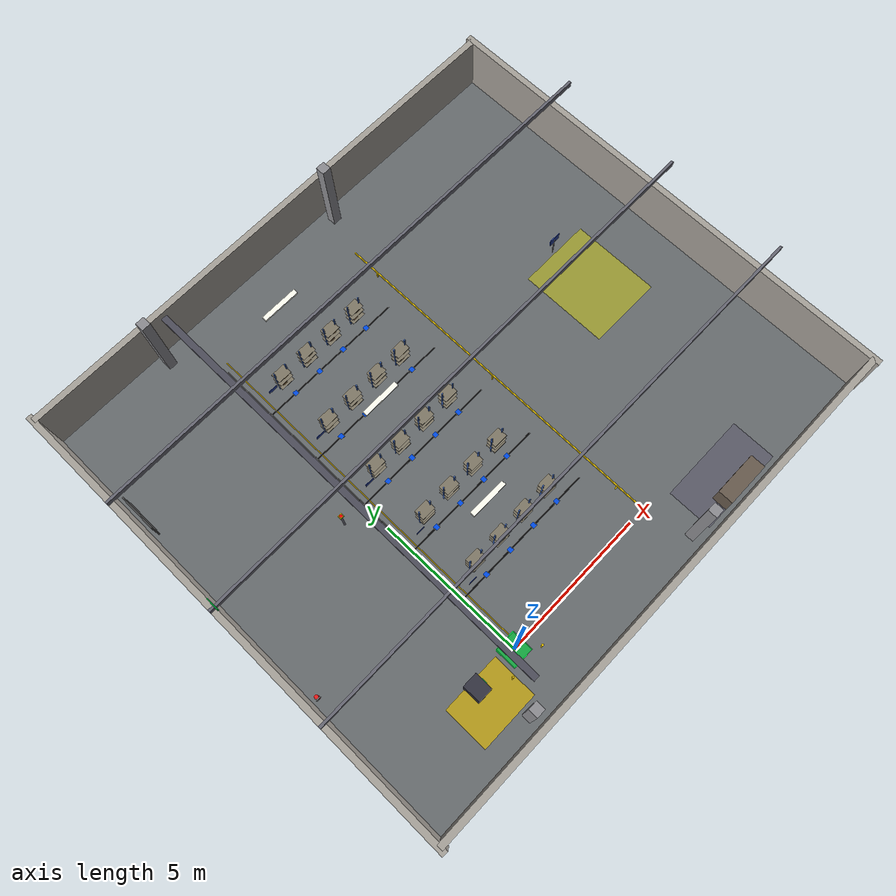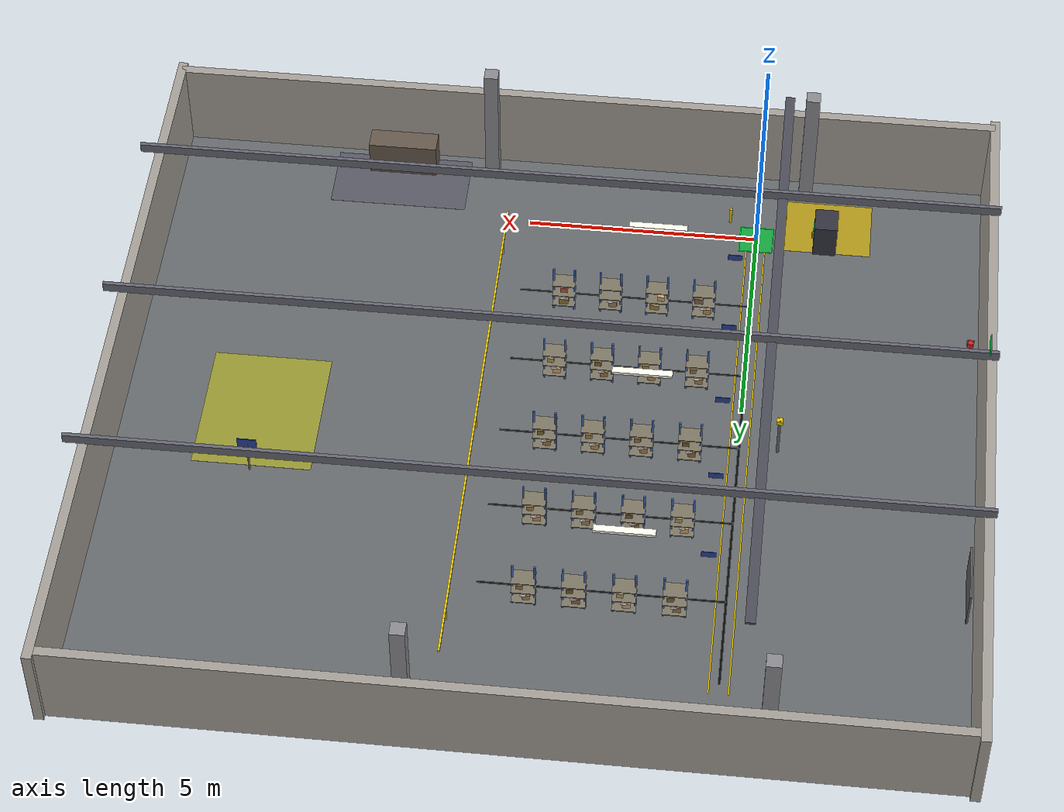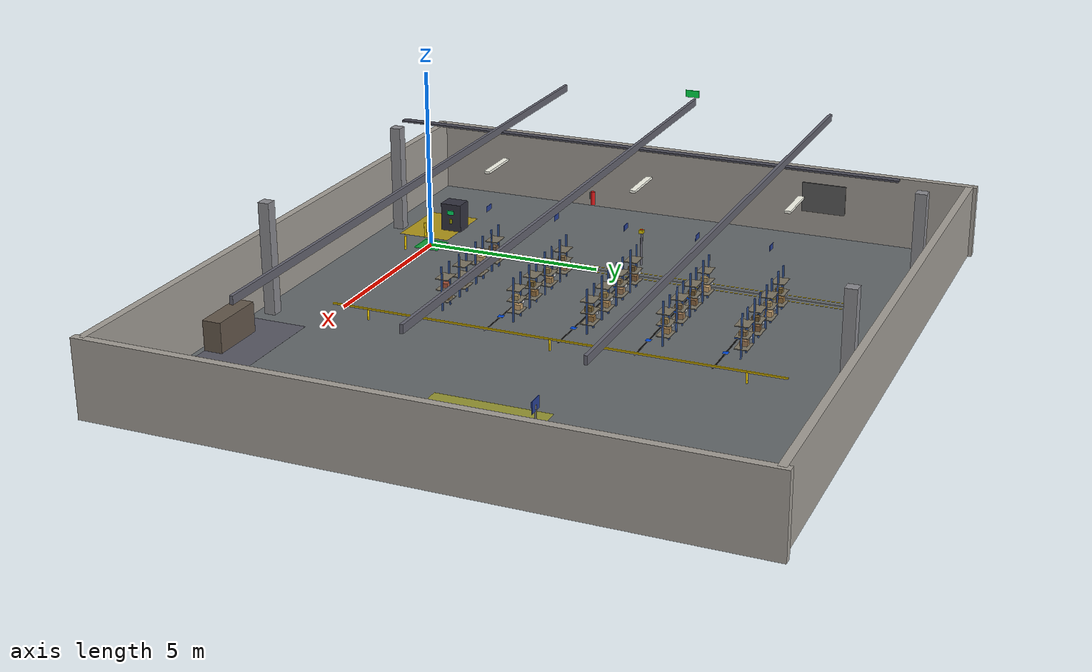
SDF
<?xml version='1.0' encoding='utf-8'?>
<sdf version="1.6">
<world name="atlas_warehouse">

  <gravity>0 0 -9.81</gravity>
  <physics type="ode">
    <max_step_size>0.001</max_step_size>
    <real_time_factor>1.0</real_time_factor>
    <real_time_update_rate>1000</real_time_update_rate>
    <ode>
      <solver><type>quick</type><iters>50</iters></solver>
    </ode>
  </physics>

  <scene>
    <ambient>0.4 0.4 0.45 1</ambient>
    <background>0.15 0.15 0.2 1</background>
    <shadows>1</shadows>
  </scene>

  <light name="led_bay_1" type="point">
    <pose>2 3 3.5 0 0 0</pose>
    <diffuse>0.95 0.92 0.85 1</diffuse>
    <specular>0.3 0.3 0.3 1</specular>
    <attenuation><range>12</range><constant>0.3</constant><linear>0.05</linear><quadratic>0.01</quadratic></attenuation>
    <cast_shadows>true</cast_shadows>
  </light>
  <light name="led_bay_2" type="point">
    <pose>2 7 3.5 0 0 0</pose>
    <diffuse>0.95 0.92 0.85 1</diffuse>
    <specular>0.3 0.3 0.3 1</specular>
    <attenuation><range>12</range><constant>0.3</constant><linear>0.05</linear><quadratic>0.01</quadratic></attenuation>
    <cast_shadows>true</cast_shadows>
  </light>
  <light name="led_bay_3" type="point">
    <pose>2 11 3.5 0 0 0</pose>
    <diffuse>0.95 0.92 0.85 1</diffuse>
    <specular>0.3 0.3 0.3 1</specular>
    <attenuation><range>12</range><constant>0.3</constant><linear>0.05</linear><quadratic>0.01</quadratic></attenuation>
    <cast_shadows>false</cast_shadows>
  </light>
  <light name="led_dock" type="spot">
    <pose>0 0 3.0 0 1.5708 0</pose>
    <diffuse>0.8 0.9 1.0 1</diffuse>
    <specular>0.2 0.2 0.3 1</specular>
    <attenuation><range>6</range><constant>0.5</constant><linear>0.1</linear><quadratic>0.02</quadratic></attenuation>
    <spot><inner_angle>0.5</inner_angle><outer_angle>1.0</outer_angle><falloff>1.0</falloff></spot>
    <cast_shadows>true</cast_shadows>
  </light>
  <light name="ambient_fill" type="directional">
    <pose>5 6 8 0 0 0</pose>
    <diffuse>0.25 0.25 0.28 1</diffuse>
    <specular>0.05 0.05 0.05 1</specular>
    <direction>-0.2 -0.1 -1</direction>
    <cast_shadows>false</cast_shadows>
  </light>

  <model name="floor_main"><static>true</static>
    <pose>4 6 -0.01 0 0 0</pose>
    <link name="link">
      <collision name="c"><geometry><box><size>18 16 0.02</size></box></geometry></collision>
      <visual name="v"><geometry><box><size>18 16 0.02</size></box></geometry>
        <material>
          <ambient>0.35 0.37 0.38 1</ambient>
          <diffuse>0.4 0.42 0.43 1</diffuse>
          <specular>0.15 0.15 0.15 1</specular>
        </material>
      </visual>
    </link>
  </model>

  <model name="lane_spine_L"><static>true</static>
    <pose>-0.2 6 0.001 0 0 0</pose>
    <link name="link">
      <visual name="v"><geometry><box><size>0.03 12.5 0.001</size></box></geometry>
        <material><ambient>0.85 0.7 0.0 1</ambient><diffuse>0.9 0.75 0.0 1</diffuse></material>
      </visual>
    </link>
  </model>
  <model name="lane_spine_R"><static>true</static>
    <pose>0.2 6 0.001 0 0 0</pose>
    <link name="link">
      <visual name="v"><geometry><box><size>0.03 12.5 0.001</size></box></geometry>
        <material><ambient>0.85 0.7 0.0 1</ambient><diffuse>0.9 0.75 0.0 1</diffuse></material>
      </visual>
    </link>
  </model>

  <model name="loading_zone"><static>true</static>
    <pose>-1.5 -0.5 0.001 0 0 0</pose>
    <link name="link">
      <visual name="v"><geometry><box><size>2.0 1.5 0.001</size></box></geometry>
        <material><ambient>0.6 0.55 0.15 1</ambient><diffuse>0.7 0.6 0.1 1</diffuse></material>
      </visual>
    </link>
  </model>

  <model name="spine_line"><static>true</static>
    <pose>0 6 0.001 0 0 0</pose>
    <link name="link">
      <collision name="c"><geometry><box><size>0.05 12 0.002</size></box></geometry></collision>
      <visual name="v"><geometry><box><size>0.05 12 0.002</size></box></geometry>
        <material><ambient>0.02 0.02 0.02 1</ambient><diffuse>0.03 0.03 0.03 1</diffuse></material>
      </visual>
    </link>
  </model>
  <model name="aisle_1"><static>true</static>
    <pose>2.5 2 0.001 0 0 0</pose>
    <link name="link">
      <collision name="c"><geometry><box><size>5 0.05 0.002</size></box></geometry></collision>
      <visual name="v"><geometry><box><size>5 0.05 0.002</size></box></geometry>
        <material><ambient>0.02 0.02 0.02 1</ambient><diffuse>0.03 0.03 0.03 1</diffuse></material>
      </visual>
    </link>
  </model>
  <model name="aisle_2"><static>true</static>
    <pose>2.5 4 0.001 0 0 0</pose>
    <link name="link">
      <collision name="c"><geometry><box><size>5 0.05 0.002</size></box></geometry></collision>
      <visual name="v"><geometry><box><size>5 0.05 0.002</size></box></geometry>
        <material><ambient>0.02 0.02 0.02 1</ambient><diffuse>0.03 0.03 0.03 1</diffuse></material>
      </visual>
    </link>
  </model>
  <model name="aisle_3"><static>true</static>
    <pose>2.5 6 0.001 0 0 0</pose>
    <link name="link">
      <collision name="c"><geometry><box><size>5 0.05 0.002</size></box></geometry></collision>
      <visual name="v"><geometry><box><size>5 0.05 0.002</size></box></geometry>
        <material><ambient>0.02 0.02 0.02 1</ambient><diffuse>0.03 0.03 0.03 1</diffuse></material>
      </visual>
    </link>
  </model>
  <model name="aisle_4"><static>true</static>
    <pose>2.5 8 0.001 0 0 0</pose>
    <link name="link">
      <collision name="c"><geometry><box><size>5 0.05 0.002</size></box></geometry></collision>
      <visual name="v"><geometry><box><size>5 0.05 0.002</size></box></geometry>
        <material><ambient>0.02 0.02 0.02 1</ambient><diffuse>0.03 0.03 0.03 1</diffuse></material>
      </visual>
    </link>
  </model>
  <model name="aisle_5"><static>true</static>
    <pose>2.5 10 0.001 0 0 0</pose>
    <link name="link">
      <collision name="c"><geometry><box><size>5 0.05 0.002</size></box></geometry></collision>
      <visual name="v"><geometry><box><size>5 0.05 0.002</size></box></geometry>
        <material><ambient>0.02 0.02 0.02 1</ambient><diffuse>0.03 0.03 0.03 1</diffuse></material>
      </visual>
    </link>
  </model>

  <model name="home_dock"><static>true</static>
    <pose>0 0 0.001 0 0 0</pose>
    <link name="link">
      <collision name="c"><geometry><box><size>0.7 0.7 0.002</size></box></geometry></collision>
      <visual name="v"><geometry><box><size>0.7 0.7 0.002</size></box></geometry>
        <material><ambient>0.05 0.55 0.2 1</ambient><diffuse>0.08 0.65 0.25 1</diffuse></material>
      </visual>
    </link>
  </model>

  <model name="dock_border_n"><static>true</static>
    <pose>0 0.36 0.003 0 0 0</pose>
    <link name="link">
      <visual name="v"><geometry><box><size>0.72 0.02 0.004</size></box></geometry>
        <material><ambient>0.0 1.0 0.3 1</ambient><diffuse>0.0 1.0 0.3 1</diffuse></material>
      </visual>
    </link>
  </model>
  <model name="dock_border_s"><static>true</static>
    <pose>0 -0.36 0.003 0 0 0</pose>
    <link name="link">
      <visual name="v"><geometry><box><size>0.72 0.02 0.004</size></box></geometry>
        <material><ambient>0.0 1.0 0.3 1</ambient><diffuse>0.0 1.0 0.3 1</diffuse></material>
      </visual>
    </link>
  </model>
  <model name="dock_border_e"><static>true</static>
    <pose>0.36 0 0.003 0 0 0</pose>
    <link name="link">
      <visual name="v"><geometry><box><size>0.02 0.72 0.004</size></box></geometry>
        <material><ambient>0.0 1.0 0.3 1</ambient><diffuse>0.0 1.0 0.3 1</diffuse></material>
      </visual>
    </link>
  </model>
  <model name="dock_border_w"><static>true</static>
    <pose>-0.36 0 0.003 0 0 0</pose>
    <link name="link">
      <visual name="v"><geometry><box><size>0.02 0.72 0.004</size></box></geometry>
        <material><ambient>0.0 1.0 0.3 1</ambient><diffuse>0.0 1.0 0.3 1</diffuse></material>
      </visual>
    </link>
  </model>

  <model name="charger_cabinet"><static>true</static>
    <pose>-1.5 0 0.4 0 0 0</pose>
    <link name="link">
      <collision name="c"><geometry><box><size>0.5 0.6 0.8</size></box></geometry></collision>
      <visual name="v"><geometry><box><size>0.5 0.6 0.8</size></box></geometry>
        <material><ambient>0.15 0.15 0.2 1</ambient><diffuse>0.2 0.2 0.25 1</diffuse><specular>0.3 0.3 0.3 1</specular></material>
      </visual>
    </link>
  </model>
  <model name="charger_display"><static>true</static>
    <pose>-1.24 0 0.55 0 0 0</pose>
    <link name="link">
      <visual name="v"><geometry><box><size>0.02 0.2 0.12</size></box></geometry>
        <material><ambient>0.0 0.8 0.3 1</ambient><diffuse>0.0 0.9 0.4 1</diffuse><emissive>0.0 0.5 0.2 1</emissive></material>
      </visual>
    </link>
  </model>
  <model name="charger_connector"><static>true</static>
    <pose>-1.24 0 0.3 0 0 0</pose>
    <link name="link">
      <visual name="v"><geometry><cylinder><radius>0.04</radius><length>0.12</length></cylinder></geometry>
        <material><ambient>0.4 0.4 0.0 1</ambient><diffuse>0.5 0.5 0.0 1</diffuse></material>
      </visual>
    </link>
  </model>

  <model name="wall_north"><static>true</static>
    <pose>4 14 1.0 0 0 0</pose>
    <link name="link">
      <collision name="c"><geometry><box><size>18 0.2 2.0</size></box></geometry></collision>
      <visual name="v"><geometry><box><size>18 0.2 2.0</size></box></geometry>
        <material><ambient>0.6 0.58 0.55 1</ambient><diffuse>0.65 0.63 0.6 1</diffuse></material>
      </visual>
    </link>
  </model>
  <model name="wall_south"><static>true</static>
    <pose>4 -2 1.0 0 0 0</pose>
    <link name="link">
      <collision name="c"><geometry><box><size>18 0.2 2.0</size></box></geometry></collision>
      <visual name="v"><geometry><box><size>18 0.2 2.0</size></box></geometry>
        <material><ambient>0.6 0.58 0.55 1</ambient><diffuse>0.65 0.63 0.6 1</diffuse></material>
      </visual>
    </link>
  </model>
  <model name="wall_east"><static>true</static>
    <pose>13 6 1.0 0 0 0</pose>
    <link name="link">
      <collision name="c"><geometry><box><size>0.2 16.4 2.0</size></box></geometry></collision>
      <visual name="v"><geometry><box><size>0.2 16.4 2.0</size></box></geometry>
        <material><ambient>0.6 0.58 0.55 1</ambient><diffuse>0.65 0.63 0.6 1</diffuse></material>
      </visual>
    </link>
  </model>
  <model name="wall_west"><static>true</static>
    <pose>-5 6 1.0 0 0 0</pose>
    <link name="link">
      <collision name="c"><geometry><box><size>0.2 16.4 2.0</size></box></geometry></collision>
      <visual name="v"><geometry><box><size>0.2 16.4 2.0</size></box></geometry>
        <material><ambient>0.6 0.58 0.55 1</ambient><diffuse>0.65 0.63 0.6 1</diffuse></material>
      </visual>
    </link>
  </model>

  <model name="col_1"><static>true</static>
    <pose>-1 -1.5 1.5 0 0 0</pose>
    <link name="link">
      <collision name="c"><geometry><box><size>0.3 0.3 3.0</size></box></geometry></collision>
      <visual name="v"><geometry><box><size>0.3 0.3 3.0</size></box></geometry>
        <material><ambient>0.5 0.5 0.52 1</ambient><diffuse>0.55 0.55 0.57 1</diffuse></material>
      </visual>
    </link>
  </model>
  <model name="col_2"><static>true</static>
    <pose>6 -1.5 1.5 0 0 0</pose>
    <link name="link">
      <collision name="c"><geometry><box><size>0.3 0.3 3.0</size></box></geometry></collision>
      <visual name="v"><geometry><box><size>0.3 0.3 3.0</size></box></geometry>
        <material><ambient>0.5 0.5 0.52 1</ambient><diffuse>0.55 0.55 0.57 1</diffuse></material>
      </visual>
    </link>
  </model>
  <model name="col_3"><static>true</static>
    <pose>-1 13.5 1.5 0 0 0</pose>
    <link name="link">
      <collision name="c"><geometry><box><size>0.3 0.3 3.0</size></box></geometry></collision>
      <visual name="v"><geometry><box><size>0.3 0.3 3.0</size></box></geometry>
        <material><ambient>0.5 0.5 0.52 1</ambient><diffuse>0.55 0.55 0.57 1</diffuse></material>
      </visual>
    </link>
  </model>
  <model name="col_4"><static>true</static>
    <pose>6 13.5 1.5 0 0 0</pose>
    <link name="link">
      <collision name="c"><geometry><box><size>0.3 0.3 3.0</size></box></geometry></collision>
      <visual name="v"><geometry><box><size>0.3 0.3 3.0</size></box></geometry>
        <material><ambient>0.5 0.5 0.52 1</ambient><diffuse>0.55 0.55 0.57 1</diffuse></material>
      </visual>
    </link>
  </model>

  <model name="truss_1"><static>true</static>
    <pose>4 2 3.5 0 0 0</pose>
    <link name="link">
      <visual name="v"><geometry><box><size>18 0.08 0.2</size></box></geometry>
        <material><ambient>0.3 0.3 0.35 1</ambient><diffuse>0.4 0.4 0.45 1</diffuse><specular>0.2 0.2 0.2 1</specular></material>
      </visual>
    </link>
  </model>
  <model name="truss_2"><static>true</static>
    <pose>4 6 3.5 0 0 0</pose>
    <link name="link">
      <visual name="v"><geometry><box><size>18 0.08 0.2</size></box></geometry>
        <material><ambient>0.3 0.3 0.35 1</ambient><diffuse>0.4 0.4 0.45 1</diffuse><specular>0.2 0.2 0.2 1</specular></material>
      </visual>
    </link>
  </model>
  <model name="truss_3"><static>true</static>
    <pose>4 10 3.5 0 0 0</pose>
    <link name="link">
      <visual name="v"><geometry><box><size>18 0.08 0.2</size></box></geometry>
        <material><ambient>0.3 0.3 0.35 1</ambient><diffuse>0.4 0.4 0.45 1</diffuse><specular>0.2 0.2 0.2 1</specular></material>
      </visual>
    </link>
  </model>

  <model name="light_fix_1"><static>true</static>
    <pose>2 3 3.3 0 0 0</pose>
    <link name="link">
      <visual name="v"><geometry><box><size>1.2 0.15 0.06</size></box></geometry>
        <material><ambient>0.9 0.9 0.85 1</ambient><diffuse>1.0 1.0 0.95 1</diffuse><emissive>0.8 0.8 0.7 1</emissive></material>
      </visual>
    </link>
  </model>
  <model name="light_fix_2"><static>true</static>
    <pose>2 7 3.3 0 0 0</pose>
    <link name="link">
      <visual name="v"><geometry><box><size>1.2 0.15 0.06</size></box></geometry>
        <material><ambient>0.9 0.9 0.85 1</ambient><diffuse>1.0 1.0 0.95 1</diffuse><emissive>0.8 0.8 0.7 1</emissive></material>
      </visual>
    </link>
  </model>
  <model name="light_fix_3"><static>true</static>
    <pose>2 11 3.3 0 0 0</pose>
    <link name="link">
      <visual name="v"><geometry><box><size>1.2 0.15 0.06</size></box></geometry>
        <material><ambient>0.9 0.9 0.85 1</ambient><diffuse>1.0 1.0 0.95 1</diffuse><emissive>0.8 0.8 0.7 1</emissive></material>
      </visual>
    </link>
  </model>

  <model name="cable_tray"><static>true</static>
    <pose>-0.5 6 3.4 0 0 0</pose>
    <link name="link">
      <visual name="v"><geometry><box><size>0.2 14 0.05</size></box></geometry>
        <material><ambient>0.25 0.25 0.3 1</ambient><diffuse>0.3 0.3 0.35 1</diffuse></material>
      </visual>
    </link>
  </model>

  <model name="rack_A1_S01"><static>true</static>
    <pose>1.0 2.45 0.0 0 0 0</pose>
    <link name="link">
      <visual name="uL"><pose>-0.22 0 0.6 0 0 0</pose><geometry><box><size>0.04 0.04 1.2</size></box></geometry><material><ambient>0.2 0.35 0.6 1</ambient><diffuse>0.25 0.4 0.7 1</diffuse><specular>0.3 0.3 0.3 1</specular></material></visual>
      <visual name="uR"><pose>0.22 0 0.6 0 0 0</pose><geometry><box><size>0.04 0.04 1.2</size></box></geometry><material><ambient>0.2 0.35 0.6 1</ambient><diffuse>0.25 0.4 0.7 1</diffuse><specular>0.3 0.3 0.3 1</specular></material></visual>
      <visual name="s1"><pose>0 0 0.25 0 0 0</pose><geometry><box><size>0.48 0.35 0.02</size></box></geometry><material><ambient>0.45 0.42 0.35 1</ambient><diffuse>0.5 0.47 0.4 1</diffuse></material></visual>
      <visual name="s2"><pose>0 0 0.55 0 0 0</pose><geometry><box><size>0.48 0.35 0.02</size></box></geometry><material><ambient>0.45 0.42 0.35 1</ambient><diffuse>0.5 0.47 0.4 1</diffuse></material></visual>
      <visual name="s3"><pose>0 0 0.85 0 0 0</pose><geometry><box><size>0.48 0.35 0.02</size></box></geometry><material><ambient>0.45 0.42 0.35 1</ambient><diffuse>0.5 0.47 0.4 1</diffuse></material></visual>
      <visual name="b1"><pose>-0.08 0 0.33 0 0 0</pose><geometry><box><size>0.16 0.22 0.14</size></box></geometry><material><ambient>0.6 0.5 0.3 1</ambient><diffuse>0.7 0.55 0.35 1</diffuse></material></visual>
      <visual name="b2"><pose>0.1 0 0.63 0 0 0</pose><geometry><box><size>0.18 0.2 0.14</size></box></geometry><material><ambient>0.4 0.35 0.25 1</ambient><diffuse>0.5 0.4 0.3 1</diffuse></material></visual>
      <visual name="lbl"><pose>0 0.18 0.5 0 0 0</pose><geometry><box><size>0.12 0.005 0.06</size></box></geometry><material><ambient>0.95 0.95 0.95 1</ambient><diffuse>1.0 1.0 1.0 1</diffuse></material></visual>
      <collision name="c"><pose>0 0 0.6 0 0 0</pose><geometry><box><size>0.5 0.36 1.2</size></box></geometry></collision>
    </link>
  </model>

  <model name="rack_A1_S02"><static>true</static>
    <pose>2.0 2.45 0.0 0 0 0</pose>
    <link name="link">
      <visual name="uL"><pose>-0.22 0 0.6 0 0 0</pose><geometry><box><size>0.04 0.04 1.2</size></box></geometry><material><ambient>0.2 0.35 0.6 1</ambient><diffuse>0.25 0.4 0.7 1</diffuse><specular>0.3 0.3 0.3 1</specular></material></visual>
      <visual name="uR"><pose>0.22 0 0.6 0 0 0</pose><geometry><box><size>0.04 0.04 1.2</size></box></geometry><material><ambient>0.2 0.35 0.6 1</ambient><diffuse>0.25 0.4 0.7 1</diffuse><specular>0.3 0.3 0.3 1</specular></material></visual>
      <visual name="s1"><pose>0 0 0.25 0 0 0</pose><geometry><box><size>0.48 0.35 0.02</size></box></geometry><material><ambient>0.45 0.42 0.35 1</ambient><diffuse>0.5 0.47 0.4 1</diffuse></material></visual>
      <visual name="s2"><pose>0 0 0.55 0 0 0</pose><geometry><box><size>0.48 0.35 0.02</size></box></geometry><material><ambient>0.45 0.42 0.35 1</ambient><diffuse>0.5 0.47 0.4 1</diffuse></material></visual>
      <visual name="s3"><pose>0 0 0.85 0 0 0</pose><geometry><box><size>0.48 0.35 0.02</size></box></geometry><material><ambient>0.45 0.42 0.35 1</ambient><diffuse>0.5 0.47 0.4 1</diffuse></material></visual>
      <visual name="b1"><pose>0.05 0 0.33 0 0 0</pose><geometry><box><size>0.2 0.18 0.14</size></box></geometry><material><ambient>0.5 0.4 0.2 1</ambient><diffuse>0.6 0.5 0.25 1</diffuse></material></visual>
      <visual name="b2"><pose>-0.08 0 0.63 0 0 0</pose><geometry><box><size>0.15 0.22 0.12</size></box></geometry><material><ambient>0.7 0.6 0.4 1</ambient><diffuse>0.8 0.65 0.45 1</diffuse></material></visual>
      <visual name="lbl"><pose>0 0.18 0.5 0 0 0</pose><geometry><box><size>0.12 0.005 0.06</size></box></geometry><material><ambient>0.95 0.95 0.95 1</ambient><diffuse>1.0 1.0 1.0 1</diffuse></material></visual>
      <collision name="c"><pose>0 0 0.6 0 0 0</pose><geometry><box><size>0.5 0.36 1.2</size></box></geometry></collision>
    </link>
  </model>

  <model name="rack_A1_S03"><static>true</static>
    <pose>3.0 2.45 0.0 0 0 0</pose>
    <link name="link">
      <visual name="uL"><pose>-0.22 0 0.6 0 0 0</pose><geometry><box><size>0.04 0.04 1.2</size></box></geometry><material><ambient>0.2 0.35 0.6 1</ambient><diffuse>0.25 0.4 0.7 1</diffuse><specular>0.3 0.3 0.3 1</specular></material></visual>
      <visual name="uR"><pose>0.22 0 0.6 0 0 0</pose><geometry><box><size>0.04 0.04 1.2</size></box></geometry><material><ambient>0.2 0.35 0.6 1</ambient><diffuse>0.25 0.4 0.7 1</diffuse><specular>0.3 0.3 0.3 1</specular></material></visual>
      <visual name="s1"><pose>0 0 0.25 0 0 0</pose><geometry><box><size>0.48 0.35 0.02</size></box></geometry><material><ambient>0.45 0.42 0.35 1</ambient><diffuse>0.5 0.47 0.4 1</diffuse></material></visual>
      <visual name="s2"><pose>0 0 0.55 0 0 0</pose><geometry><box><size>0.48 0.35 0.02</size></box></geometry><material><ambient>0.45 0.42 0.35 1</ambient><diffuse>0.5 0.47 0.4 1</diffuse></material></visual>
      <visual name="s3"><pose>0 0 0.85 0 0 0</pose><geometry><box><size>0.48 0.35 0.02</size></box></geometry><material><ambient>0.45 0.42 0.35 1</ambient><diffuse>0.5 0.47 0.4 1</diffuse></material></visual>
      <visual name="b1"><pose>-0.05 0 0.33 0 0 0</pose><geometry><box><size>0.18 0.2 0.14</size></box></geometry><material><ambient>0.55 0.45 0.3 1</ambient><diffuse>0.6 0.5 0.35 1</diffuse></material></visual>
      <visual name="lbl"><pose>0 0.18 0.5 0 0 0</pose><geometry><box><size>0.12 0.005 0.06</size></box></geometry><material><ambient>0.95 0.95 0.95 1</ambient><diffuse>1.0 1.0 1.0 1</diffuse></material></visual>
      <collision name="c"><pose>0 0 0.6 0 0 0</pose><geometry><box><size>0.5 0.36 1.2</size></box></geometry></collision>
    </link>
  </model>

  <model name="rack_A1_S04"><static>true</static>
    <pose>4.0 2.45 0.0 0 0 0</pose>
    <link name="link">
      <visual name="uL"><pose>-0.22 0 0.6 0 0 0</pose><geometry><box><size>0.04 0.04 1.2</size></box></geometry><material><ambient>0.2 0.35 0.6 1</ambient><diffuse>0.25 0.4 0.7 1</diffuse><specular>0.3 0.3 0.3 1</specular></material></visual>
      <visual name="uR"><pose>0.22 0 0.6 0 0 0</pose><geometry><box><size>0.04 0.04 1.2</size></box></geometry><material><ambient>0.2 0.35 0.6 1</ambient><diffuse>0.25 0.4 0.7 1</diffuse><specular>0.3 0.3 0.3 1</specular></material></visual>
      <visual name="s1"><pose>0 0 0.25 0 0 0</pose><geometry><box><size>0.48 0.35 0.02</size></box></geometry><material><ambient>0.45 0.42 0.35 1</ambient><diffuse>0.5 0.47 0.4 1</diffuse></material></visual>
      <visual name="s2"><pose>0 0 0.55 0 0 0</pose><geometry><box><size>0.48 0.35 0.02</size></box></geometry><material><ambient>0.45 0.42 0.35 1</ambient><diffuse>0.5 0.47 0.4 1</diffuse></material></visual>
      <visual name="s3"><pose>0 0 0.85 0 0 0</pose><geometry><box><size>0.48 0.35 0.02</size></box></geometry><material><ambient>0.45 0.42 0.35 1</ambient><diffuse>0.5 0.47 0.4 1</diffuse></material></visual>
      <visual name="b1"><pose>0.0 0 0.33 0 0 0</pose><geometry><box><size>0.2 0.25 0.14</size></box></geometry><material><ambient>0.45 0.35 0.2 1</ambient><diffuse>0.55 0.45 0.25 1</diffuse></material></visual>
      <visual name="b2"><pose>0.0 0 0.63 0 0 0</pose><geometry><box><size>0.15 0.15 0.12</size></box></geometry><material><ambient>0.6 0.3 0.2 1</ambient><diffuse>0.7 0.35 0.25 1</diffuse></material></visual>
      <visual name="lbl"><pose>0 0.18 0.5 0 0 0</pose><geometry><box><size>0.12 0.005 0.06</size></box></geometry><material><ambient>0.95 0.95 0.95 1</ambient><diffuse>1.0 1.0 1.0 1</diffuse></material></visual>
      <collision name="c"><pose>0 0 0.6 0 0 0</pose><geometry><box><size>0.5 0.36 1.2</size></box></geometry></collision>
    </link>
  </model>

  <model name="rack_A2_S05"><static>true</static>
    <pose>1.0 4.45 0.0 0 0 0</pose>
    <link name="link">
      <visual name="uL"><pose>-0.22 0 0.6 0 0 0</pose><geometry><box><size>0.04 0.04 1.2</size></box></geometry><material><ambient>0.2 0.35 0.6 1</ambient><diffuse>0.25 0.4 0.7 1</diffuse><specular>0.3 0.3 0.3 1</specular></material></visual>
      <visual name="uR"><pose>0.22 0 0.6 0 0 0</pose><geometry><box><size>0.04 0.04 1.2</size></box></geometry><material><ambient>0.2 0.35 0.6 1</ambient><diffuse>0.25 0.4 0.7 1</diffuse><specular>0.3 0.3 0.3 1</specular></material></visual>
      <visual name="s1"><pose>0 0 0.25 0 0 0</pose><geometry><box><size>0.48 0.35 0.02</size></box></geometry><material><ambient>0.45 0.42 0.35 1</ambient><diffuse>0.5 0.47 0.4 1</diffuse></material></visual>
      <visual name="s2"><pose>0 0 0.55 0 0 0</pose><geometry><box><size>0.48 0.35 0.02</size></box></geometry><material><ambient>0.45 0.42 0.35 1</ambient><diffuse>0.5 0.47 0.4 1</diffuse></material></visual>
      <visual name="s3"><pose>0 0 0.85 0 0 0</pose><geometry><box><size>0.48 0.35 0.02</size></box></geometry><material><ambient>0.45 0.42 0.35 1</ambient><diffuse>0.5 0.47 0.4 1</diffuse></material></visual>
      <visual name="b1"><pose>-0.05 0 0.33 0 0 0</pose><geometry><box><size>0.16 0.2 0.14</size></box></geometry><material><ambient>0.55 0.45 0.3 1</ambient><diffuse>0.65 0.5 0.35 1</diffuse></material></visual>
      <visual name="b2"><pose>0.08 0 0.63 0 0 0</pose><geometry><box><size>0.14 0.18 0.12</size></box></geometry><material><ambient>0.45000000000000007 0.4 0.25 1</ambient><diffuse>0.55 0.45 0.3 1</diffuse></material></visual>
      <visual name="lbl"><pose>0 0.18 0.5 0 0 0</pose><geometry><box><size>0.12 0.005 0.06</size></box></geometry><material><ambient>0.95 0.95 0.95 1</ambient><diffuse>1.0 1.0 1.0 1</diffuse></material></visual>
      <collision name="c"><pose>0 0 0.6 0 0 0</pose><geometry><box><size>0.5 0.36 1.2</size></box></geometry></collision>
    </link>
  </model>
  <model name="rack_A2_S06"><static>true</static>
    <pose>2.0 4.45 0.0 0 0 0</pose>
    <link name="link">
      <visual name="uL"><pose>-0.22 0 0.6 0 0 0</pose><geometry><box><size>0.04 0.04 1.2</size></box></geometry><material><ambient>0.2 0.35 0.6 1</ambient><diffuse>0.25 0.4 0.7 1</diffuse><specular>0.3 0.3 0.3 1</specular></material></visual>
      <visual name="uR"><pose>0.22 0 0.6 0 0 0</pose><geometry><box><size>0.04 0.04 1.2</size></box></geometry><material><ambient>0.2 0.35 0.6 1</ambient><diffuse>0.25 0.4 0.7 1</diffuse><specular>0.3 0.3 0.3 1</specular></material></visual>
      <visual name="s1"><pose>0 0 0.25 0 0 0</pose><geometry><box><size>0.48 0.35 0.02</size></box></geometry><material><ambient>0.45 0.42 0.35 1</ambient><diffuse>0.5 0.47 0.4 1</diffuse></material></visual>
      <visual name="s2"><pose>0 0 0.55 0 0 0</pose><geometry><box><size>0.48 0.35 0.02</size></box></geometry><material><ambient>0.45 0.42 0.35 1</ambient><diffuse>0.5 0.47 0.4 1</diffuse></material></visual>
      <visual name="s3"><pose>0 0 0.85 0 0 0</pose><geometry><box><size>0.48 0.35 0.02</size></box></geometry><material><ambient>0.45 0.42 0.35 1</ambient><diffuse>0.5 0.47 0.4 1</diffuse></material></visual>
      <visual name="b1"><pose>-0.05 0 0.33 0 0 0</pose><geometry><box><size>0.16 0.2 0.14</size></box></geometry><material><ambient>0.6 0.5 0.3 1</ambient><diffuse>0.7 0.55 0.35 1</diffuse></material></visual>
      <visual name="b2"><pose>0.08 0 0.63 0 0 0</pose><geometry><box><size>0.14 0.18 0.12</size></box></geometry><material><ambient>0.5 0.45 0.25 1</ambient><diffuse>0.6 0.5 0.3 1</diffuse></material></visual>
      <visual name="lbl"><pose>0 0.18 0.5 0 0 0</pose><geometry><box><size>0.12 0.005 0.06</size></box></geometry><material><ambient>0.95 0.95 0.95 1</ambient><diffuse>1.0 1.0 1.0 1</diffuse></material></visual>
      <collision name="c"><pose>0 0 0.6 0 0 0</pose><geometry><box><size>0.5 0.36 1.2</size></box></geometry></collision>
    </link>
  </model>
  <model name="rack_A2_S07"><static>true</static>
    <pose>3.0 4.45 0.0 0 0 0</pose>
    <link name="link">
      <visual name="uL"><pose>-0.22 0 0.6 0 0 0</pose><geometry><box><size>0.04 0.04 1.2</size></box></geometry><material><ambient>0.2 0.35 0.6 1</ambient><diffuse>0.25 0.4 0.7 1</diffuse><specular>0.3 0.3 0.3 1</specular></material></visual>
      <visual name="uR"><pose>0.22 0 0.6 0 0 0</pose><geometry><box><size>0.04 0.04 1.2</size></box></geometry><material><ambient>0.2 0.35 0.6 1</ambient><diffuse>0.25 0.4 0.7 1</diffuse><specular>0.3 0.3 0.3 1</specular></material></visual>
      <visual name="s1"><pose>0 0 0.25 0 0 0</pose><geometry><box><size>0.48 0.35 0.02</size></box></geometry><material><ambient>0.45 0.42 0.35 1</ambient><diffuse>0.5 0.47 0.4 1</diffuse></material></visual>
      <visual name="s2"><pose>0 0 0.55 0 0 0</pose><geometry><box><size>0.48 0.35 0.02</size></box></geometry><material><ambient>0.45 0.42 0.35 1</ambient><diffuse>0.5 0.47 0.4 1</diffuse></material></visual>
      <visual name="s3"><pose>0 0 0.85 0 0 0</pose><geometry><box><size>0.48 0.35 0.02</size></box></geometry><material><ambient>0.45 0.42 0.35 1</ambient><diffuse>0.5 0.47 0.4 1</diffuse></material></visual>
      <visual name="b1"><pose>-0.05 0 0.33 0 0 0</pose><geometry><box><size>0.16 0.2 0.14</size></box></geometry><material><ambient>0.5 0.4 0.2 1</ambient><diffuse>0.6 0.45 0.25 1</diffuse></material></visual>
      <visual name="b2"><pose>0.08 0 0.63 0 0 0</pose><geometry><box><size>0.14 0.18 0.12</size></box></geometry><material><ambient>0.4 0.35000000000000003 0.15000000000000002 1</ambient><diffuse>0.5 0.4 0.2 1</diffuse></material></visual>
      <visual name="lbl"><pose>0 0.18 0.5 0 0 0</pose><geometry><box><size>0.12 0.005 0.06</size></box></geometry><material><ambient>0.95 0.95 0.95 1</ambient><diffuse>1.0 1.0 1.0 1</diffuse></material></visual>
      <collision name="c"><pose>0 0 0.6 0 0 0</pose><geometry><box><size>0.5 0.36 1.2</size></box></geometry></collision>
    </link>
  </model>
  <model name="rack_A2_S08"><static>true</static>
    <pose>4.0 4.45 0.0 0 0 0</pose>
    <link name="link">
      <visual name="uL"><pose>-0.22 0 0.6 0 0 0</pose><geometry><box><size>0.04 0.04 1.2</size></box></geometry><material><ambient>0.2 0.35 0.6 1</ambient><diffuse>0.25 0.4 0.7 1</diffuse><specular>0.3 0.3 0.3 1</specular></material></visual>
      <visual name="uR"><pose>0.22 0 0.6 0 0 0</pose><geometry><box><size>0.04 0.04 1.2</size></box></geometry><material><ambient>0.2 0.35 0.6 1</ambient><diffuse>0.25 0.4 0.7 1</diffuse><specular>0.3 0.3 0.3 1</specular></material></visual>
      <visual name="s1"><pose>0 0 0.25 0 0 0</pose><geometry><box><size>0.48 0.35 0.02</size></box></geometry><material><ambient>0.45 0.42 0.35 1</ambient><diffuse>0.5 0.47 0.4 1</diffuse></material></visual>
      <visual name="s2"><pose>0 0 0.55 0 0 0</pose><geometry><box><size>0.48 0.35 0.02</size></box></geometry><material><ambient>0.45 0.42 0.35 1</ambient><diffuse>0.5 0.47 0.4 1</diffuse></material></visual>
      <visual name="s3"><pose>0 0 0.85 0 0 0</pose><geometry><box><size>0.48 0.35 0.02</size></box></geometry><material><ambient>0.45 0.42 0.35 1</ambient><diffuse>0.5 0.47 0.4 1</diffuse></material></visual>
      <visual name="b1"><pose>-0.05 0 0.33 0 0 0</pose><geometry><box><size>0.16 0.2 0.14</size></box></geometry><material><ambient>0.7 0.6 0.4 1</ambient><diffuse>0.7999999999999999 0.65 0.45 1</diffuse></material></visual>
      <visual name="b2"><pose>0.08 0 0.63 0 0 0</pose><geometry><box><size>0.14 0.18 0.12</size></box></geometry><material><ambient>0.6 0.5499999999999999 0.35000000000000003 1</ambient><diffuse>0.7 0.6 0.4 1</diffuse></material></visual>
      <visual name="lbl"><pose>0 0.18 0.5 0 0 0</pose><geometry><box><size>0.12 0.005 0.06</size></box></geometry><material><ambient>0.95 0.95 0.95 1</ambient><diffuse>1.0 1.0 1.0 1</diffuse></material></visual>
      <collision name="c"><pose>0 0 0.6 0 0 0</pose><geometry><box><size>0.5 0.36 1.2</size></box></geometry></collision>
    </link>
  </model>

  <model name="rack_A3_S09"><static>true</static>
    <pose>1.0 6.45 0.0 0 0 0</pose>
    <link name="link">
      <visual name="uL"><pose>-0.22 0 0.6 0 0 0</pose><geometry><box><size>0.04 0.04 1.2</size></box></geometry><material><ambient>0.2 0.35 0.6 1</ambient><diffuse>0.25 0.4 0.7 1</diffuse><specular>0.3 0.3 0.3 1</specular></material></visual>
      <visual name="uR"><pose>0.22 0 0.6 0 0 0</pose><geometry><box><size>0.04 0.04 1.2</size></box></geometry><material><ambient>0.2 0.35 0.6 1</ambient><diffuse>0.25 0.4 0.7 1</diffuse><specular>0.3 0.3 0.3 1</specular></material></visual>
      <visual name="s1"><pose>0 0 0.25 0 0 0</pose><geometry><box><size>0.48 0.35 0.02</size></box></geometry><material><ambient>0.45 0.42 0.35 1</ambient><diffuse>0.5 0.47 0.4 1</diffuse></material></visual>
      <visual name="s2"><pose>0 0 0.55 0 0 0</pose><geometry><box><size>0.48 0.35 0.02</size></box></geometry><material><ambient>0.45 0.42 0.35 1</ambient><diffuse>0.5 0.47 0.4 1</diffuse></material></visual>
      <visual name="s3"><pose>0 0 0.85 0 0 0</pose><geometry><box><size>0.48 0.35 0.02</size></box></geometry><material><ambient>0.45 0.42 0.35 1</ambient><diffuse>0.5 0.47 0.4 1</diffuse></material></visual>
      <visual name="b1"><pose>-0.05 0 0.33 0 0 0</pose><geometry><box><size>0.16 0.2 0.14</size></box></geometry><material><ambient>0.45 0.35 0.2 1</ambient><diffuse>0.55 0.39999999999999997 0.25 1</diffuse></material></visual>
      <visual name="b2"><pose>0.08 0 0.63 0 0 0</pose><geometry><box><size>0.14 0.18 0.12</size></box></geometry><material><ambient>0.35 0.3 0.15000000000000002 1</ambient><diffuse>0.45 0.35 0.2 1</diffuse></material></visual>
      <visual name="lbl"><pose>0 0.18 0.5 0 0 0</pose><geometry><box><size>0.12 0.005 0.06</size></box></geometry><material><ambient>0.95 0.95 0.95 1</ambient><diffuse>1.0 1.0 1.0 1</diffuse></material></visual>
      <collision name="c"><pose>0 0 0.6 0 0 0</pose><geometry><box><size>0.5 0.36 1.2</size></box></geometry></collision>
    </link>
  </model>
  <model name="rack_A3_S10"><static>true</static>
    <pose>2.0 6.45 0.0 0 0 0</pose>
    <link name="link">
      <visual name="uL"><pose>-0.22 0 0.6 0 0 0</pose><geometry><box><size>0.04 0.04 1.2</size></box></geometry><material><ambient>0.2 0.35 0.6 1</ambient><diffuse>0.25 0.4 0.7 1</diffuse><specular>0.3 0.3 0.3 1</specular></material></visual>
      <visual name="uR"><pose>0.22 0 0.6 0 0 0</pose><geometry><box><size>0.04 0.04 1.2</size></box></geometry><material><ambient>0.2 0.35 0.6 1</ambient><diffuse>0.25 0.4 0.7 1</diffuse><specular>0.3 0.3 0.3 1</specular></material></visual>
      <visual name="s1"><pose>0 0 0.25 0 0 0</pose><geometry><box><size>0.48 0.35 0.02</size></box></geometry><material><ambient>0.45 0.42 0.35 1</ambient><diffuse>0.5 0.47 0.4 1</diffuse></material></visual>
      <visual name="s2"><pose>0 0 0.55 0 0 0</pose><geometry><box><size>0.48 0.35 0.02</size></box></geometry><material><ambient>0.45 0.42 0.35 1</ambient><diffuse>0.5 0.47 0.4 1</diffuse></material></visual>
      <visual name="s3"><pose>0 0 0.85 0 0 0</pose><geometry><box><size>0.48 0.35 0.02</size></box></geometry><material><ambient>0.45 0.42 0.35 1</ambient><diffuse>0.5 0.47 0.4 1</diffuse></material></visual>
      <visual name="b1"><pose>-0.05 0 0.33 0 0 0</pose><geometry><box><size>0.16 0.2 0.14</size></box></geometry><material><ambient>0.55 0.45 0.3 1</ambient><diffuse>0.65 0.5 0.35 1</diffuse></material></visual>
      <visual name="b2"><pose>0.08 0 0.63 0 0 0</pose><geometry><box><size>0.14 0.18 0.12</size></box></geometry><material><ambient>0.45000000000000007 0.4 0.25 1</ambient><diffuse>0.55 0.45 0.3 1</diffuse></material></visual>
      <visual name="lbl"><pose>0 0.18 0.5 0 0 0</pose><geometry><box><size>0.12 0.005 0.06</size></box></geometry><material><ambient>0.95 0.95 0.95 1</ambient><diffuse>1.0 1.0 1.0 1</diffuse></material></visual>
      <collision name="c"><pose>0 0 0.6 0 0 0</pose><geometry><box><size>0.5 0.36 1.2</size></box></geometry></collision>
    </link>
  </model>
  <model name="rack_A3_S11"><static>true</static>
    <pose>3.0 6.45 0.0 0 0 0</pose>
    <link name="link">
      <visual name="uL"><pose>-0.22 0 0.6 0 0 0</pose><geometry><box><size>0.04 0.04 1.2</size></box></geometry><material><ambient>0.2 0.35 0.6 1</ambient><diffuse>0.25 0.4 0.7 1</diffuse><specular>0.3 0.3 0.3 1</specular></material></visual>
      <visual name="uR"><pose>0.22 0 0.6 0 0 0</pose><geometry><box><size>0.04 0.04 1.2</size></box></geometry><material><ambient>0.2 0.35 0.6 1</ambient><diffuse>0.25 0.4 0.7 1</diffuse><specular>0.3 0.3 0.3 1</specular></material></visual>
      <visual name="s1"><pose>0 0 0.25 0 0 0</pose><geometry><box><size>0.48 0.35 0.02</size></box></geometry><material><ambient>0.45 0.42 0.35 1</ambient><diffuse>0.5 0.47 0.4 1</diffuse></material></visual>
      <visual name="s2"><pose>0 0 0.55 0 0 0</pose><geometry><box><size>0.48 0.35 0.02</size></box></geometry><material><ambient>0.45 0.42 0.35 1</ambient><diffuse>0.5 0.47 0.4 1</diffuse></material></visual>
      <visual name="s3"><pose>0 0 0.85 0 0 0</pose><geometry><box><size>0.48 0.35 0.02</size></box></geometry><material><ambient>0.45 0.42 0.35 1</ambient><diffuse>0.5 0.47 0.4 1</diffuse></material></visual>
      <visual name="b1"><pose>-0.05 0 0.33 0 0 0</pose><geometry><box><size>0.16 0.2 0.14</size></box></geometry><material><ambient>0.6 0.5 0.3 1</ambient><diffuse>0.7 0.55 0.35 1</diffuse></material></visual>
      <visual name="b2"><pose>0.08 0 0.63 0 0 0</pose><geometry><box><size>0.14 0.18 0.12</size></box></geometry><material><ambient>0.5 0.45 0.25 1</ambient><diffuse>0.6 0.5 0.3 1</diffuse></material></visual>
      <visual name="lbl"><pose>0 0.18 0.5 0 0 0</pose><geometry><box><size>0.12 0.005 0.06</size></box></geometry><material><ambient>0.95 0.95 0.95 1</ambient><diffuse>1.0 1.0 1.0 1</diffuse></material></visual>
      <collision name="c"><pose>0 0 0.6 0 0 0</pose><geometry><box><size>0.5 0.36 1.2</size></box></geometry></collision>
    </link>
  </model>
  <model name="rack_A3_S12"><static>true</static>
    <pose>4.0 6.45 0.0 0 0 0</pose>
    <link name="link">
      <visual name="uL"><pose>-0.22 0 0.6 0 0 0</pose><geometry><box><size>0.04 0.04 1.2</size></box></geometry><material><ambient>0.2 0.35 0.6 1</ambient><diffuse>0.25 0.4 0.7 1</diffuse><specular>0.3 0.3 0.3 1</specular></material></visual>
      <visual name="uR"><pose>0.22 0 0.6 0 0 0</pose><geometry><box><size>0.04 0.04 1.2</size></box></geometry><material><ambient>0.2 0.35 0.6 1</ambient><diffuse>0.25 0.4 0.7 1</diffuse><specular>0.3 0.3 0.3 1</specular></material></visual>
      <visual name="s1"><pose>0 0 0.25 0 0 0</pose><geometry><box><size>0.48 0.35 0.02</size></box></geometry><material><ambient>0.45 0.42 0.35 1</ambient><diffuse>0.5 0.47 0.4 1</diffuse></material></visual>
      <visual name="s2"><pose>0 0 0.55 0 0 0</pose><geometry><box><size>0.48 0.35 0.02</size></box></geometry><material><ambient>0.45 0.42 0.35 1</ambient><diffuse>0.5 0.47 0.4 1</diffuse></material></visual>
      <visual name="s3"><pose>0 0 0.85 0 0 0</pose><geometry><box><size>0.48 0.35 0.02</size></box></geometry><material><ambient>0.45 0.42 0.35 1</ambient><diffuse>0.5 0.47 0.4 1</diffuse></material></visual>
      <visual name="b1"><pose>-0.05 0 0.33 0 0 0</pose><geometry><box><size>0.16 0.2 0.14</size></box></geometry><material><ambient>0.5 0.4 0.2 1</ambient><diffuse>0.6 0.45 0.25 1</diffuse></material></visual>
      <visual name="b2"><pose>0.08 0 0.63 0 0 0</pose><geometry><box><size>0.14 0.18 0.12</size></box></geometry><material><ambient>0.4 0.35000000000000003 0.15000000000000002 1</ambient><diffuse>0.5 0.4 0.2 1</diffuse></material></visual>
      <visual name="lbl"><pose>0 0.18 0.5 0 0 0</pose><geometry><box><size>0.12 0.005 0.06</size></box></geometry><material><ambient>0.95 0.95 0.95 1</ambient><diffuse>1.0 1.0 1.0 1</diffuse></material></visual>
      <collision name="c"><pose>0 0 0.6 0 0 0</pose><geometry><box><size>0.5 0.36 1.2</size></box></geometry></collision>
    </link>
  </model>

  <model name="rack_A4_S13"><static>true</static>
    <pose>1.0 8.45 0.0 0 0 0</pose>
    <link name="link">
      <visual name="uL"><pose>-0.22 0 0.6 0 0 0</pose><geometry><box><size>0.04 0.04 1.2</size></box></geometry><material><ambient>0.2 0.35 0.6 1</ambient><diffuse>0.25 0.4 0.7 1</diffuse><specular>0.3 0.3 0.3 1</specular></material></visual>
      <visual name="uR"><pose>0.22 0 0.6 0 0 0</pose><geometry><box><size>0.04 0.04 1.2</size></box></geometry><material><ambient>0.2 0.35 0.6 1</ambient><diffuse>0.25 0.4 0.7 1</diffuse><specular>0.3 0.3 0.3 1</specular></material></visual>
      <visual name="s1"><pose>0 0 0.25 0 0 0</pose><geometry><box><size>0.48 0.35 0.02</size></box></geometry><material><ambient>0.45 0.42 0.35 1</ambient><diffuse>0.5 0.47 0.4 1</diffuse></material></visual>
      <visual name="s2"><pose>0 0 0.55 0 0 0</pose><geometry><box><size>0.48 0.35 0.02</size></box></geometry><material><ambient>0.45 0.42 0.35 1</ambient><diffuse>0.5 0.47 0.4 1</diffuse></material></visual>
      <visual name="s3"><pose>0 0 0.85 0 0 0</pose><geometry><box><size>0.48 0.35 0.02</size></box></geometry><material><ambient>0.45 0.42 0.35 1</ambient><diffuse>0.5 0.47 0.4 1</diffuse></material></visual>
      <visual name="b1"><pose>-0.05 0 0.33 0 0 0</pose><geometry><box><size>0.16 0.2 0.14</size></box></geometry><material><ambient>0.7 0.6 0.4 1</ambient><diffuse>0.7999999999999999 0.65 0.45 1</diffuse></material></visual>
      <visual name="b2"><pose>0.08 0 0.63 0 0 0</pose><geometry><box><size>0.14 0.18 0.12</size></box></geometry><material><ambient>0.6 0.5499999999999999 0.35000000000000003 1</ambient><diffuse>0.7 0.6 0.4 1</diffuse></material></visual>
      <visual name="lbl"><pose>0 0.18 0.5 0 0 0</pose><geometry><box><size>0.12 0.005 0.06</size></box></geometry><material><ambient>0.95 0.95 0.95 1</ambient><diffuse>1.0 1.0 1.0 1</diffuse></material></visual>
      <collision name="c"><pose>0 0 0.6 0 0 0</pose><geometry><box><size>0.5 0.36 1.2</size></box></geometry></collision>
    </link>
  </model>
  <model name="rack_A4_S14"><static>true</static>
    <pose>2.0 8.45 0.0 0 0 0</pose>
    <link name="link">
      <visual name="uL"><pose>-0.22 0 0.6 0 0 0</pose><geometry><box><size>0.04 0.04 1.2</size></box></geometry><material><ambient>0.2 0.35 0.6 1</ambient><diffuse>0.25 0.4 0.7 1</diffuse><specular>0.3 0.3 0.3 1</specular></material></visual>
      <visual name="uR"><pose>0.22 0 0.6 0 0 0</pose><geometry><box><size>0.04 0.04 1.2</size></box></geometry><material><ambient>0.2 0.35 0.6 1</ambient><diffuse>0.25 0.4 0.7 1</diffuse><specular>0.3 0.3 0.3 1</specular></material></visual>
      <visual name="s1"><pose>0 0 0.25 0 0 0</pose><geometry><box><size>0.48 0.35 0.02</size></box></geometry><material><ambient>0.45 0.42 0.35 1</ambient><diffuse>0.5 0.47 0.4 1</diffuse></material></visual>
      <visual name="s2"><pose>0 0 0.55 0 0 0</pose><geometry><box><size>0.48 0.35 0.02</size></box></geometry><material><ambient>0.45 0.42 0.35 1</ambient><diffuse>0.5 0.47 0.4 1</diffuse></material></visual>
      <visual name="s3"><pose>0 0 0.85 0 0 0</pose><geometry><box><size>0.48 0.35 0.02</size></box></geometry><material><ambient>0.45 0.42 0.35 1</ambient><diffuse>0.5 0.47 0.4 1</diffuse></material></visual>
      <visual name="b1"><pose>-0.05 0 0.33 0 0 0</pose><geometry><box><size>0.16 0.2 0.14</size></box></geometry><material><ambient>0.45 0.35 0.2 1</ambient><diffuse>0.55 0.39999999999999997 0.25 1</diffuse></material></visual>
      <visual name="b2"><pose>0.08 0 0.63 0 0 0</pose><geometry><box><size>0.14 0.18 0.12</size></box></geometry><material><ambient>0.35 0.3 0.15000000000000002 1</ambient><diffuse>0.45 0.35 0.2 1</diffuse></material></visual>
      <visual name="lbl"><pose>0 0.18 0.5 0 0 0</pose><geometry><box><size>0.12 0.005 0.06</size></box></geometry><material><ambient>0.95 0.95 0.95 1</ambient><diffuse>1.0 1.0 1.0 1</diffuse></material></visual>
      <collision name="c"><pose>0 0 0.6 0 0 0</pose><geometry><box><size>0.5 0.36 1.2</size></box></geometry></collision>
    </link>
  </model>
  <model name="rack_A4_S15"><static>true</static>
    <pose>3.0 8.45 0.0 0 0 0</pose>
    <link name="link">
      <visual name="uL"><pose>-0.22 0 0.6 0 0 0</pose><geometry><box><size>0.04 0.04 1.2</size></box></geometry><material><ambient>0.2 0.35 0.6 1</ambient><diffuse>0.25 0.4 0.7 1</diffuse><specular>0.3 0.3 0.3 1</specular></material></visual>
      <visual name="uR"><pose>0.22 0 0.6 0 0 0</pose><geometry><box><size>0.04 0.04 1.2</size></box></geometry><material><ambient>0.2 0.35 0.6 1</ambient><diffuse>0.25 0.4 0.7 1</diffuse><specular>0.3 0.3 0.3 1</specular></material></visual>
      <visual name="s1"><pose>0 0 0.25 0 0 0</pose><geometry><box><size>0.48 0.35 0.02</size></box></geometry><material><ambient>0.45 0.42 0.35 1</ambient><diffuse>0.5 0.47 0.4 1</diffuse></material></visual>
      <visual name="s2"><pose>0 0 0.55 0 0 0</pose><geometry><box><size>0.48 0.35 0.02</size></box></geometry><material><ambient>0.45 0.42 0.35 1</ambient><diffuse>0.5 0.47 0.4 1</diffuse></material></visual>
      <visual name="s3"><pose>0 0 0.85 0 0 0</pose><geometry><box><size>0.48 0.35 0.02</size></box></geometry><material><ambient>0.45 0.42 0.35 1</ambient><diffuse>0.5 0.47 0.4 1</diffuse></material></visual>
      <visual name="b1"><pose>-0.05 0 0.33 0 0 0</pose><geometry><box><size>0.16 0.2 0.14</size></box></geometry><material><ambient>0.55 0.45 0.3 1</ambient><diffuse>0.65 0.5 0.35 1</diffuse></material></visual>
      <visual name="b2"><pose>0.08 0 0.63 0 0 0</pose><geometry><box><size>0.14 0.18 0.12</size></box></geometry><material><ambient>0.45000000000000007 0.4 0.25 1</ambient><diffuse>0.55 0.45 0.3 1</diffuse></material></visual>
      <visual name="lbl"><pose>0 0.18 0.5 0 0 0</pose><geometry><box><size>0.12 0.005 0.06</size></box></geometry><material><ambient>0.95 0.95 0.95 1</ambient><diffuse>1.0 1.0 1.0 1</diffuse></material></visual>
      <collision name="c"><pose>0 0 0.6 0 0 0</pose><geometry><box><size>0.5 0.36 1.2</size></box></geometry></collision>
    </link>
  </model>
  <model name="rack_A4_S16"><static>true</static>
    <pose>4.0 8.45 0.0 0 0 0</pose>
    <link name="link">
      <visual name="uL"><pose>-0.22 0 0.6 0 0 0</pose><geometry><box><size>0.04 0.04 1.2</size></box></geometry><material><ambient>0.2 0.35 0.6 1</ambient><diffuse>0.25 0.4 0.7 1</diffuse><specular>0.3 0.3 0.3 1</specular></material></visual>
      <visual name="uR"><pose>0.22 0 0.6 0 0 0</pose><geometry><box><size>0.04 0.04 1.2</size></box></geometry><material><ambient>0.2 0.35 0.6 1</ambient><diffuse>0.25 0.4 0.7 1</diffuse><specular>0.3 0.3 0.3 1</specular></material></visual>
      <visual name="s1"><pose>0 0 0.25 0 0 0</pose><geometry><box><size>0.48 0.35 0.02</size></box></geometry><material><ambient>0.45 0.42 0.35 1</ambient><diffuse>0.5 0.47 0.4 1</diffuse></material></visual>
      <visual name="s2"><pose>0 0 0.55 0 0 0</pose><geometry><box><size>0.48 0.35 0.02</size></box></geometry><material><ambient>0.45 0.42 0.35 1</ambient><diffuse>0.5 0.47 0.4 1</diffuse></material></visual>
      <visual name="s3"><pose>0 0 0.85 0 0 0</pose><geometry><box><size>0.48 0.35 0.02</size></box></geometry><material><ambient>0.45 0.42 0.35 1</ambient><diffuse>0.5 0.47 0.4 1</diffuse></material></visual>
      <visual name="b1"><pose>-0.05 0 0.33 0 0 0</pose><geometry><box><size>0.16 0.2 0.14</size></box></geometry><material><ambient>0.6 0.5 0.3 1</ambient><diffuse>0.7 0.55 0.35 1</diffuse></material></visual>
      <visual name="b2"><pose>0.08 0 0.63 0 0 0</pose><geometry><box><size>0.14 0.18 0.12</size></box></geometry><material><ambient>0.5 0.45 0.25 1</ambient><diffuse>0.6 0.5 0.3 1</diffuse></material></visual>
      <visual name="lbl"><pose>0 0.18 0.5 0 0 0</pose><geometry><box><size>0.12 0.005 0.06</size></box></geometry><material><ambient>0.95 0.95 0.95 1</ambient><diffuse>1.0 1.0 1.0 1</diffuse></material></visual>
      <collision name="c"><pose>0 0 0.6 0 0 0</pose><geometry><box><size>0.5 0.36 1.2</size></box></geometry></collision>
    </link>
  </model>

  <model name="rack_A5_S17"><static>true</static>
    <pose>1.0 10.45 0.0 0 0 0</pose>
    <link name="link">
      <visual name="uL"><pose>-0.22 0 0.6 0 0 0</pose><geometry><box><size>0.04 0.04 1.2</size></box></geometry><material><ambient>0.2 0.35 0.6 1</ambient><diffuse>0.25 0.4 0.7 1</diffuse><specular>0.3 0.3 0.3 1</specular></material></visual>
      <visual name="uR"><pose>0.22 0 0.6 0 0 0</pose><geometry><box><size>0.04 0.04 1.2</size></box></geometry><material><ambient>0.2 0.35 0.6 1</ambient><diffuse>0.25 0.4 0.7 1</diffuse><specular>0.3 0.3 0.3 1</specular></material></visual>
      <visual name="s1"><pose>0 0 0.25 0 0 0</pose><geometry><box><size>0.48 0.35 0.02</size></box></geometry><material><ambient>0.45 0.42 0.35 1</ambient><diffuse>0.5 0.47 0.4 1</diffuse></material></visual>
      <visual name="s2"><pose>0 0 0.55 0 0 0</pose><geometry><box><size>0.48 0.35 0.02</size></box></geometry><material><ambient>0.45 0.42 0.35 1</ambient><diffuse>0.5 0.47 0.4 1</diffuse></material></visual>
      <visual name="s3"><pose>0 0 0.85 0 0 0</pose><geometry><box><size>0.48 0.35 0.02</size></box></geometry><material><ambient>0.45 0.42 0.35 1</ambient><diffuse>0.5 0.47 0.4 1</diffuse></material></visual>
      <visual name="b1"><pose>-0.05 0 0.33 0 0 0</pose><geometry><box><size>0.16 0.2 0.14</size></box></geometry><material><ambient>0.5 0.4 0.2 1</ambient><diffuse>0.6 0.45 0.25 1</diffuse></material></visual>
      <visual name="b2"><pose>0.08 0 0.63 0 0 0</pose><geometry><box><size>0.14 0.18 0.12</size></box></geometry><material><ambient>0.4 0.35000000000000003 0.15000000000000002 1</ambient><diffuse>0.5 0.4 0.2 1</diffuse></material></visual>
      <visual name="lbl"><pose>0 0.18 0.5 0 0 0</pose><geometry><box><size>0.12 0.005 0.06</size></box></geometry><material><ambient>0.95 0.95 0.95 1</ambient><diffuse>1.0 1.0 1.0 1</diffuse></material></visual>
      <collision name="c"><pose>0 0 0.6 0 0 0</pose><geometry><box><size>0.5 0.36 1.2</size></box></geometry></collision>
    </link>
  </model>
  <model name="rack_A5_S18"><static>true</static>
    <pose>2.0 10.45 0.0 0 0 0</pose>
    <link name="link">
      <visual name="uL"><pose>-0.22 0 0.6 0 0 0</pose><geometry><box><size>0.04 0.04 1.2</size></box></geometry><material><ambient>0.2 0.35 0.6 1</ambient><diffuse>0.25 0.4 0.7 1</diffuse><specular>0.3 0.3 0.3 1</specular></material></visual>
      <visual name="uR"><pose>0.22 0 0.6 0 0 0</pose><geometry><box><size>0.04 0.04 1.2</size></box></geometry><material><ambient>0.2 0.35 0.6 1</ambient><diffuse>0.25 0.4 0.7 1</diffuse><specular>0.3 0.3 0.3 1</specular></material></visual>
      <visual name="s1"><pose>0 0 0.25 0 0 0</pose><geometry><box><size>0.48 0.35 0.02</size></box></geometry><material><ambient>0.45 0.42 0.35 1</ambient><diffuse>0.5 0.47 0.4 1</diffuse></material></visual>
      <visual name="s2"><pose>0 0 0.55 0 0 0</pose><geometry><box><size>0.48 0.35 0.02</size></box></geometry><material><ambient>0.45 0.42 0.35 1</ambient><diffuse>0.5 0.47 0.4 1</diffuse></material></visual>
      <visual name="s3"><pose>0 0 0.85 0 0 0</pose><geometry><box><size>0.48 0.35 0.02</size></box></geometry><material><ambient>0.45 0.42 0.35 1</ambient><diffuse>0.5 0.47 0.4 1</diffuse></material></visual>
      <visual name="b1"><pose>-0.05 0 0.33 0 0 0</pose><geometry><box><size>0.16 0.2 0.14</size></box></geometry><material><ambient>0.7 0.6 0.4 1</ambient><diffuse>0.7999999999999999 0.65 0.45 1</diffuse></material></visual>
      <visual name="b2"><pose>0.08 0 0.63 0 0 0</pose><geometry><box><size>0.14 0.18 0.12</size></box></geometry><material><ambient>0.6 0.5499999999999999 0.35000000000000003 1</ambient><diffuse>0.7 0.6 0.4 1</diffuse></material></visual>
      <visual name="lbl"><pose>0 0.18 0.5 0 0 0</pose><geometry><box><size>0.12 0.005 0.06</size></box></geometry><material><ambient>0.95 0.95 0.95 1</ambient><diffuse>1.0 1.0 1.0 1</diffuse></material></visual>
      <collision name="c"><pose>0 0 0.6 0 0 0</pose><geometry><box><size>0.5 0.36 1.2</size></box></geometry></collision>
    </link>
  </model>
  <model name="rack_A5_S19"><static>true</static>
    <pose>3.0 10.45 0.0 0 0 0</pose>
    <link name="link">
      <visual name="uL"><pose>-0.22 0 0.6 0 0 0</pose><geometry><box><size>0.04 0.04 1.2</size></box></geometry><material><ambient>0.2 0.35 0.6 1</ambient><diffuse>0.25 0.4 0.7 1</diffuse><specular>0.3 0.3 0.3 1</specular></material></visual>
      <visual name="uR"><pose>0.22 0 0.6 0 0 0</pose><geometry><box><size>0.04 0.04 1.2</size></box></geometry><material><ambient>0.2 0.35 0.6 1</ambient><diffuse>0.25 0.4 0.7 1</diffuse><specular>0.3 0.3 0.3 1</specular></material></visual>
      <visual name="s1"><pose>0 0 0.25 0 0 0</pose><geometry><box><size>0.48 0.35 0.02</size></box></geometry><material><ambient>0.45 0.42 0.35 1</ambient><diffuse>0.5 0.47 0.4 1</diffuse></material></visual>
      <visual name="s2"><pose>0 0 0.55 0 0 0</pose><geometry><box><size>0.48 0.35 0.02</size></box></geometry><material><ambient>0.45 0.42 0.35 1</ambient><diffuse>0.5 0.47 0.4 1</diffuse></material></visual>
      <visual name="s3"><pose>0 0 0.85 0 0 0</pose><geometry><box><size>0.48 0.35 0.02</size></box></geometry><material><ambient>0.45 0.42 0.35 1</ambient><diffuse>0.5 0.47 0.4 1</diffuse></material></visual>
      <visual name="b1"><pose>-0.05 0 0.33 0 0 0</pose><geometry><box><size>0.16 0.2 0.14</size></box></geometry><material><ambient>0.45 0.35 0.2 1</ambient><diffuse>0.55 0.39999999999999997 0.25 1</diffuse></material></visual>
      <visual name="b2"><pose>0.08 0 0.63 0 0 0</pose><geometry><box><size>0.14 0.18 0.12</size></box></geometry><material><ambient>0.35 0.3 0.15000000000000002 1</ambient><diffuse>0.45 0.35 0.2 1</diffuse></material></visual>
      <visual name="lbl"><pose>0 0.18 0.5 0 0 0</pose><geometry><box><size>0.12 0.005 0.06</size></box></geometry><material><ambient>0.95 0.95 0.95 1</ambient><diffuse>1.0 1.0 1.0 1</diffuse></material></visual>
      <collision name="c"><pose>0 0 0.6 0 0 0</pose><geometry><box><size>0.5 0.36 1.2</size></box></geometry></collision>
    </link>
  </model>
  <model name="rack_A5_S20"><static>true</static>
    <pose>4.0 10.45 0.0 0 0 0</pose>
    <link name="link">
      <visual name="uL"><pose>-0.22 0 0.6 0 0 0</pose><geometry><box><size>0.04 0.04 1.2</size></box></geometry><material><ambient>0.2 0.35 0.6 1</ambient><diffuse>0.25 0.4 0.7 1</diffuse><specular>0.3 0.3 0.3 1</specular></material></visual>
      <visual name="uR"><pose>0.22 0 0.6 0 0 0</pose><geometry><box><size>0.04 0.04 1.2</size></box></geometry><material><ambient>0.2 0.35 0.6 1</ambient><diffuse>0.25 0.4 0.7 1</diffuse><specular>0.3 0.3 0.3 1</specular></material></visual>
      <visual name="s1"><pose>0 0 0.25 0 0 0</pose><geometry><box><size>0.48 0.35 0.02</size></box></geometry><material><ambient>0.45 0.42 0.35 1</ambient><diffuse>0.5 0.47 0.4 1</diffuse></material></visual>
      <visual name="s2"><pose>0 0 0.55 0 0 0</pose><geometry><box><size>0.48 0.35 0.02</size></box></geometry><material><ambient>0.45 0.42 0.35 1</ambient><diffuse>0.5 0.47 0.4 1</diffuse></material></visual>
      <visual name="s3"><pose>0 0 0.85 0 0 0</pose><geometry><box><size>0.48 0.35 0.02</size></box></geometry><material><ambient>0.45 0.42 0.35 1</ambient><diffuse>0.5 0.47 0.4 1</diffuse></material></visual>
      <visual name="b1"><pose>-0.05 0 0.33 0 0 0</pose><geometry><box><size>0.16 0.2 0.14</size></box></geometry><material><ambient>0.55 0.45 0.3 1</ambient><diffuse>0.65 0.5 0.35 1</diffuse></material></visual>
      <visual name="b2"><pose>0.08 0 0.63 0 0 0</pose><geometry><box><size>0.14 0.18 0.12</size></box></geometry><material><ambient>0.45000000000000007 0.4 0.25 1</ambient><diffuse>0.55 0.45 0.3 1</diffuse></material></visual>
      <visual name="lbl"><pose>0 0.18 0.5 0 0 0</pose><geometry><box><size>0.12 0.005 0.06</size></box></geometry><material><ambient>0.95 0.95 0.95 1</ambient><diffuse>1.0 1.0 1.0 1</diffuse></material></visual>
      <collision name="c"><pose>0 0 0.6 0 0 0</pose><geometry><box><size>0.5 0.36 1.2</size></box></geometry></collision>
    </link>
  </model>

  <model name="barrier_dock_1"><static>true</static>
    <pose>-0.6 -0.5 0.2 0 0 0</pose>
    <link name="link">
      <visual name="post"><geometry><cylinder><radius>0.03</radius><length>0.4</length></cylinder></geometry>
        <material><ambient>0.85 0.7 0.0 1</ambient><diffuse>0.95 0.8 0.0 1</diffuse></material>
      </visual>
    </link>
  </model>
  <model name="barrier_dock_2"><static>true</static>
    <pose>0.6 -0.5 0.2 0 0 0</pose>
    <link name="link">
      <visual name="post"><geometry><cylinder><radius>0.03</radius><length>0.4</length></cylinder></geometry>
        <material><ambient>0.85 0.7 0.0 1</ambient><diffuse>0.95 0.8 0.0 1</diffuse></material>
      </visual>
    </link>
  </model>
  <model name="guardrail_1"><static>true</static>
    <pose>5.5 6 0.3 0 0 0</pose>
    <link name="link">
      <visual name="rail"><geometry><box><size>0.04 12 0.04</size></box></geometry>
        <material><ambient>0.85 0.7 0.0 1</ambient><diffuse>0.95 0.8 0.0 1</diffuse></material>
      </visual>
      <visual name="post1"><pose>0 -5 -0.15 0 0 0</pose><geometry><cylinder><radius>0.025</radius><length>0.3</length></cylinder></geometry>
        <material><ambient>0.85 0.7 0.0 1</ambient><diffuse>0.95 0.8 0.0 1</diffuse></material>
      </visual>
      <visual name="post2"><pose>0 0 -0.15 0 0 0</pose><geometry><cylinder><radius>0.025</radius><length>0.3</length></cylinder></geometry>
        <material><ambient>0.85 0.7 0.0 1</ambient><diffuse>0.95 0.8 0.0 1</diffuse></material>
      </visual>
      <visual name="post3"><pose>0 5 -0.15 0 0 0</pose><geometry><cylinder><radius>0.025</radius><length>0.3</length></cylinder></geometry>
        <material><ambient>0.85 0.7 0.0 1</ambient><diffuse>0.95 0.8 0.0 1</diffuse></material>
      </visual>
    </link>
  </model>

  <model name="estop_pillar"><static>true</static>
    <pose>-0.8 6 0.0 0 0 0</pose>
    <link name="link">
      <visual name="pole"><pose>0 0 0.5 0 0 0</pose><geometry><cylinder><radius>0.03</radius><length>1.0</length></cylinder></geometry>
        <material><ambient>0.3 0.3 0.35 1</ambient><diffuse>0.4 0.4 0.45 1</diffuse></material>
      </visual>
      <visual name="button"><pose>0 0 1.0 0 0 0</pose><geometry><cylinder><radius>0.05</radius><length>0.04</length></cylinder></geometry>
        <material><ambient>0.9 0.0 0.0 1</ambient><diffuse>1.0 0.0 0.0 1</diffuse><emissive>0.3 0.0 0.0 1</emissive></material>
      </visual>
      <visual name="housing"><pose>0 0 0.97 0 0 0</pose><geometry><box><size>0.12 0.12 0.1</size></box></geometry>
        <material><ambient>0.8 0.7 0.0 1</ambient><diffuse>0.9 0.8 0.0 1</diffuse></material>
      </visual>
    </link>
  </model>

  <model name="sign_aisle1"><static>true</static>
    <pose>0.4 2 1.5 0 0 0</pose>
    <link name="link">
      <visual name="v"><geometry><box><size>0.3 0.01 0.15</size></box></geometry>
        <material><ambient>0.1 0.2 0.5 1</ambient><diffuse>0.15 0.25 0.6 1</diffuse></material>
      </visual>
    </link>
  </model>
  <model name="sign_aisle2"><static>true</static>
    <pose>0.4 4 1.5 0 0 0</pose>
    <link name="link">
      <visual name="v"><geometry><box><size>0.3 0.01 0.15</size></box></geometry>
        <material><ambient>0.1 0.2 0.5 1</ambient><diffuse>0.15 0.25 0.6 1</diffuse></material>
      </visual>
    </link>
  </model>
  <model name="sign_aisle3"><static>true</static>
    <pose>0.4 6 1.5 0 0 0</pose>
    <link name="link">
      <visual name="v"><geometry><box><size>0.3 0.01 0.15</size></box></geometry>
        <material><ambient>0.1 0.2 0.5 1</ambient><diffuse>0.15 0.25 0.6 1</diffuse></material>
      </visual>
    </link>
  </model>
  <model name="sign_aisle4"><static>true</static>
    <pose>0.4 8 1.5 0 0 0</pose>
    <link name="link">
      <visual name="v"><geometry><box><size>0.3 0.01 0.15</size></box></geometry>
        <material><ambient>0.1 0.2 0.5 1</ambient><diffuse>0.15 0.25 0.6 1</diffuse></material>
      </visual>
    </link>
  </model>
  <model name="sign_aisle5"><static>true</static>
    <pose>0.4 10 1.5 0 0 0</pose>
    <link name="link">
      <visual name="v"><geometry><box><size>0.3 0.01 0.15</size></box></geometry>
        <material><ambient>0.1 0.2 0.5 1</ambient><diffuse>0.15 0.25 0.6 1</diffuse></material>
      </visual>
    </link>
  </model>

  <model name="exit_sign"><static>true</static>
    <pose>-4.8 6 3.8 0 0 1.5708</pose>
    <link name="link">
      <visual name="v"><geometry><box><size>0.4 0.02 0.2</size></box></geometry>
        <material><ambient>0.0 0.8 0.2 1</ambient><diffuse>0.0 0.9 0.3 1</diffuse><emissive>0.0 0.4 0.1 1</emissive></material>
      </visual>
    </link>
  </model>

  <model name="fire_ext"><static>true</static>
    <pose>-4.7 3 0.0 0 0 0</pose>
    <link name="link">
      <visual name="tank"><pose>0 0 0.3 0 0 0</pose><geometry><cylinder><radius>0.06</radius><length>0.4</length></cylinder></geometry>
        <material><ambient>0.8 0.0 0.0 1</ambient><diffuse>0.9 0.1 0.1 1</diffuse></material>
      </visual>
      <visual name="bracket"><pose>0 -0.07 0.4 0 0 0</pose><geometry><box><size>0.15 0.02 0.2</size></box></geometry>
        <material><ambient>0.4 0.4 0.4 1</ambient><diffuse>0.5 0.5 0.5 1</diffuse></material>
      </visual>
    </link>
  </model>

  <model name="rfid_pad_01"><static>true</static>
    <pose>1.0 2 0.002 0 0 0</pose>
    <link name="link">
      <visual name="v"><geometry><box><size>0.15 0.15 0.002</size></box></geometry>
        <material><ambient>0.0 0.2 0.7 1</ambient><diffuse>0.0 0.3 0.9 1</diffuse><emissive>0.0 0.05 0.2 1</emissive></material>
      </visual>
    </link>
  </model>
  <model name="rfid_pad_02"><static>true</static>
    <pose>2.0 2 0.002 0 0 0</pose>
    <link name="link">
      <visual name="v"><geometry><box><size>0.15 0.15 0.002</size></box></geometry>
        <material><ambient>0.0 0.2 0.7 1</ambient><diffuse>0.0 0.3 0.9 1</diffuse><emissive>0.0 0.05 0.2 1</emissive></material>
      </visual>
    </link>
  </model>
  <model name="rfid_pad_03"><static>true</static>
    <pose>3.0 2 0.002 0 0 0</pose>
    <link name="link">
      <visual name="v"><geometry><box><size>0.15 0.15 0.002</size></box></geometry>
        <material><ambient>0.0 0.2 0.7 1</ambient><diffuse>0.0 0.3 0.9 1</diffuse><emissive>0.0 0.05 0.2 1</emissive></material>
      </visual>
    </link>
  </model>
  <model name="rfid_pad_04"><static>true</static>
    <pose>4.0 2 0.002 0 0 0</pose>
    <link name="link">
      <visual name="v"><geometry><box><size>0.15 0.15 0.002</size></box></geometry>
        <material><ambient>0.0 0.2 0.7 1</ambient><diffuse>0.0 0.3 0.9 1</diffuse><emissive>0.0 0.05 0.2 1</emissive></material>
      </visual>
    </link>
  </model>
  <model name="rfid_pad_05"><static>true</static>
    <pose>1.0 4 0.002 0 0 0</pose>
    <link name="link">
      <visual name="v"><geometry><box><size>0.15 0.15 0.002</size></box></geometry>
        <material><ambient>0.0 0.2 0.7 1</ambient><diffuse>0.0 0.3 0.9 1</diffuse><emissive>0.0 0.05 0.2 1</emissive></material>
      </visual>
    </link>
  </model>
  <model name="rfid_pad_06"><static>true</static>
    <pose>2.0 4 0.002 0 0 0</pose>
    <link name="link">
      <visual name="v"><geometry><box><size>0.15 0.15 0.002</size></box></geometry>
        <material><ambient>0.0 0.2 0.7 1</ambient><diffuse>0.0 0.3 0.9 1</diffuse><emissive>0.0 0.05 0.2 1</emissive></material>
      </visual>
    </link>
  </model>
  <model name="rfid_pad_07"><static>true</static>
    <pose>3.0 4 0.002 0 0 0</pose>
    <link name="link">
      <visual name="v"><geometry><box><size>0.15 0.15 0.002</size></box></geometry>
        <material><ambient>0.0 0.2 0.7 1</ambient><diffuse>0.0 0.3 0.9 1</diffuse><emissive>0.0 0.05 0.2 1</emissive></material>
      </visual>
    </link>
  </model>
  <model name="rfid_pad_08"><static>true</static>
    <pose>4.0 4 0.002 0 0 0</pose>
    <link name="link">
      <visual name="v"><geometry><box><size>0.15 0.15 0.002</size></box></geometry>
        <material><ambient>0.0 0.2 0.7 1</ambient><diffuse>0.0 0.3 0.9 1</diffuse><emissive>0.0 0.05 0.2 1</emissive></material>
      </visual>
    </link>
  </model>
  <model name="rfid_pad_09"><static>true</static>
    <pose>1.0 6 0.002 0 0 0</pose>
    <link name="link">
      <visual name="v"><geometry><box><size>0.15 0.15 0.002</size></box></geometry>
        <material><ambient>0.0 0.2 0.7 1</ambient><diffuse>0.0 0.3 0.9 1</diffuse><emissive>0.0 0.05 0.2 1</emissive></material>
      </visual>
    </link>
  </model>
  <model name="rfid_pad_10"><static>true</static>
    <pose>2.0 6 0.002 0 0 0</pose>
    <link name="link">
      <visual name="v"><geometry><box><size>0.15 0.15 0.002</size></box></geometry>
        <material><ambient>0.0 0.2 0.7 1</ambient><diffuse>0.0 0.3 0.9 1</diffuse><emissive>0.0 0.05 0.2 1</emissive></material>
      </visual>
    </link>
  </model>
  <model name="rfid_pad_11"><static>true</static>
    <pose>3.0 6 0.002 0 0 0</pose>
    <link name="link">
      <visual name="v"><geometry><box><size>0.15 0.15 0.002</size></box></geometry>
        <material><ambient>0.0 0.2 0.7 1</ambient><diffuse>0.0 0.3 0.9 1</diffuse><emissive>0.0 0.05 0.2 1</emissive></material>
      </visual>
    </link>
  </model>
  <model name="rfid_pad_12"><static>true</static>
    <pose>4.0 6 0.002 0 0 0</pose>
    <link name="link">
      <visual name="v"><geometry><box><size>0.15 0.15 0.002</size></box></geometry>
        <material><ambient>0.0 0.2 0.7 1</ambient><diffuse>0.0 0.3 0.9 1</diffuse><emissive>0.0 0.05 0.2 1</emissive></material>
      </visual>
    </link>
  </model>
  <model name="rfid_pad_13"><static>true</static>
    <pose>1.0 8 0.002 0 0 0</pose>
    <link name="link">
      <visual name="v"><geometry><box><size>0.15 0.15 0.002</size></box></geometry>
        <material><ambient>0.0 0.2 0.7 1</ambient><diffuse>0.0 0.3 0.9 1</diffuse><emissive>0.0 0.05 0.2 1</emissive></material>
      </visual>
    </link>
  </model>
  <model name="rfid_pad_14"><static>true</static>
    <pose>2.0 8 0.002 0 0 0</pose>
    <link name="link">
      <visual name="v"><geometry><box><size>0.15 0.15 0.002</size></box></geometry>
        <material><ambient>0.0 0.2 0.7 1</ambient><diffuse>0.0 0.3 0.9 1</diffuse><emissive>0.0 0.05 0.2 1</emissive></material>
      </visual>
    </link>
  </model>
  <model name="rfid_pad_15"><static>true</static>
    <pose>3.0 8 0.002 0 0 0</pose>
    <link name="link">
      <visual name="v"><geometry><box><size>0.15 0.15 0.002</size></box></geometry>
        <material><ambient>0.0 0.2 0.7 1</ambient><diffuse>0.0 0.3 0.9 1</diffuse><emissive>0.0 0.05 0.2 1</emissive></material>
      </visual>
    </link>
  </model>
  <model name="rfid_pad_16"><static>true</static>
    <pose>4.0 8 0.002 0 0 0</pose>
    <link name="link">
      <visual name="v"><geometry><box><size>0.15 0.15 0.002</size></box></geometry>
        <material><ambient>0.0 0.2 0.7 1</ambient><diffuse>0.0 0.3 0.9 1</diffuse><emissive>0.0 0.05 0.2 1</emissive></material>
      </visual>
    </link>
  </model>
  <model name="rfid_pad_17"><static>true</static>
    <pose>1.0 10 0.002 0 0 0</pose>
    <link name="link">
      <visual name="v"><geometry><box><size>0.15 0.15 0.002</size></box></geometry>
        <material><ambient>0.0 0.2 0.7 1</ambient><diffuse>0.0 0.3 0.9 1</diffuse><emissive>0.0 0.05 0.2 1</emissive></material>
      </visual>
    </link>
  </model>
  <model name="rfid_pad_18"><static>true</static>
    <pose>2.0 10 0.002 0 0 0</pose>
    <link name="link">
      <visual name="v"><geometry><box><size>0.15 0.15 0.002</size></box></geometry>
        <material><ambient>0.0 0.2 0.7 1</ambient><diffuse>0.0 0.3 0.9 1</diffuse><emissive>0.0 0.05 0.2 1</emissive></material>
      </visual>
    </link>
  </model>
  <model name="rfid_pad_19"><static>true</static>
    <pose>3.0 10 0.002 0 0 0</pose>
    <link name="link">
      <visual name="v"><geometry><box><size>0.15 0.15 0.002</size></box></geometry>
        <material><ambient>0.0 0.2 0.7 1</ambient><diffuse>0.0 0.3 0.9 1</diffuse><emissive>0.0 0.05 0.2 1</emissive></material>
      </visual>
    </link>
  </model>
  <model name="rfid_pad_20"><static>true</static>
    <pose>4.0 10 0.002 0 0 0</pose>
    <link name="link">
      <visual name="v"><geometry><box><size>0.15 0.15 0.002</size></box></geometry>
        <material><ambient>0.0 0.2 0.7 1</ambient><diffuse>0.0 0.3 0.9 1</diffuse><emissive>0.0 0.05 0.2 1</emissive></material>
      </visual>
    </link>
  </model>

  <model name="maint_bay"><static>true</static>
    <pose>8 -1 0.001 0 0 0</pose>
    <link name="link">
      <visual name="floor"><geometry><box><size>3 1.5 0.002</size></box></geometry>
        <material><ambient>0.3 0.3 0.35 1</ambient><diffuse>0.35 0.35 0.4 1</diffuse></material>
      </visual>
    </link>
  </model>
  <model name="maint_bench"><static>true</static>
    <pose>8 -1.5 0.4 0 0 0</pose>
    <link name="link">
      <collision name="c"><geometry><box><size>1.5 0.5 0.8</size></box></geometry></collision>
      <visual name="v"><geometry><box><size>1.5 0.5 0.8</size></box></geometry>
        <material><ambient>0.35 0.3 0.25 1</ambient><diffuse>0.4 0.35 0.3 1</diffuse></material>
      </visual>
    </link>
  </model>

  <model name="forklift_zone"><static>true</static>
    <pose>10 6 0.001 0 0 0</pose>
    <link name="link">
      <visual name="v"><geometry><box><size>2.5 3.0 0.002</size></box></geometry>
        <material><ambient>0.5 0.5 0.15 1</ambient><diffuse>0.6 0.6 0.2 1</diffuse></material>
      </visual>
    </link>
  </model>
  <model name="forklift_sign"><static>true</static>
    <pose>10 7.6 0.8 0 0 0</pose>
    <link name="link">
      <visual name="post"><pose>0 0 -0.4 0 0 0</pose><geometry><cylinder><radius>0.02</radius><length>0.8</length></cylinder></geometry>
        <material><ambient>0.4 0.4 0.4 1</ambient><diffuse>0.5 0.5 0.5 1</diffuse></material>
      </visual>
      <visual name="sign"><geometry><box><size>0.4 0.02 0.3</size></box></geometry>
        <material><ambient>0.1 0.2 0.5 1</ambient><diffuse>0.15 0.25 0.6 1</diffuse></material>
      </visual>
    </link>
  </model>

  <model name="info_board"><static>true</static>
    <pose>-4.7 10 1.2 0 0 1.5708</pose>
    <link name="link">
      <visual name="board"><geometry><box><size>1.2 0.03 0.8</size></box></geometry>
        <material><ambient>0.9 0.9 0.9 1</ambient><diffuse>0.95 0.95 0.95 1</diffuse></material>
      </visual>
      <visual name="frame"><geometry><box><size>1.25 0.04 0.85</size></box></geometry>
        <material><ambient>0.3 0.3 0.3 1</ambient><diffuse>0.35 0.35 0.35 1</diffuse></material>
      </visual>
    </link>
  </model>

</world>
</sdf>
